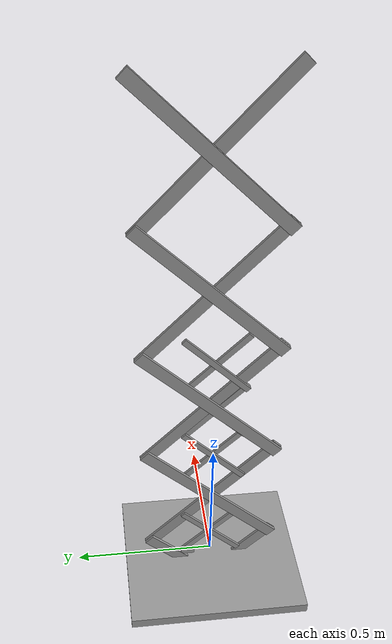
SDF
<?xml version='1.0'?>
<sdf version='1.6'>
  <model name='Robordion_leg_2'>
    <link name='link_0'>
      <pose frame=''>-0.007203 -0.002325 -0.144647 0.77 -0 0</pose>
      <inertial>
        <mass>0.00028808</mass>
        <inertia>
          <ixx>1.032e-05</ixx>
          <ixy>0</ixy>
          <ixz>0</ixz>
          <iyy>4e-08</iyy>
          <iyz>0</iyz>
          <izz>1.028e-05</izz>
        </inertia>
        <pose frame=''>0 0 0 0 -0 0</pose>
      </inertial>
      <self_collide>0</self_collide>
      <kinematic>0</kinematic>
      <enable_wind>0</enable_wind>
      <gravity>1</gravity>
      <visual name='visual'>
        <pose frame=''>0 0 0 0 -0 0</pose>
        <geometry>
          <box>
            <size>0.010804 0.654301 0.040827</size>
          </box>
        </geometry>
        <material>
          <lighting>1</lighting>
          <script>
            <uri>file://media/materials/scripts/gazebo.material</uri>
            <name>Gazebo/Grey</name>
          </script>
          <ambient>0.3 0.3 0.3 1</ambient>
          <diffuse>0.7 0.7 0.7 1</diffuse>
          <specular>0.01 0.01 0.01 1</specular>
          <emissive>0 0 0 1</emissive>
          <shader type='vertex'>
            <normal_map>__default__</normal_map>
          </shader>
        </material>
        <cast_shadows>1</cast_shadows>
        <transparency>0</transparency>
      </visual>
      <collision name='collision'>
        <laser_retro>0</laser_retro>
        <max_contacts>10</max_contacts>
        <pose frame=''>0 0 0 0 -0 0</pose>
        <geometry>
          <box>
            <size>0.010804 0.654301 0.040827</size>
          </box>
        </geometry>
        <surface>
          <friction>
            <ode>
              <mu>1</mu>
              <mu2>1</mu2>
              <fdir1>0 0 0</fdir1>
              <slip1>0</slip1>
              <slip2>0</slip2>
            </ode>
            <torsional>
              <coefficient>1</coefficient>
              <patch_radius>0</patch_radius>
              <surface_radius>0</surface_radius>
              <use_patch_radius>1</use_patch_radius>
              <ode>
                <slip>0</slip>
              </ode>
            </torsional>
          </friction>
          <bounce>
            <restitution_coefficient>0</restitution_coefficient>
            <threshold>1e+06</threshold>
          </bounce>
          <contact>
            <collide_without_contact>0</collide_without_contact>
            <collide_without_contact_bitmask>1</collide_without_contact_bitmask>
            <collide_bitmask>1</collide_bitmask>
            <ode>
              <soft_cfm>0</soft_cfm>
              <soft_erp>0.2</soft_erp>
              <kp>1e+13</kp>
              <kd>1</kd>
              <max_vel>0.01</max_vel>
              <min_depth>0</min_depth>
            </ode>
            <bullet>
              <split_impulse>1</split_impulse>
              <split_impulse_penetration_threshold>-0.01</split_impulse_penetration_threshold>
              <soft_cfm>0</soft_cfm>
              <soft_erp>0.2</soft_erp>
              <kp>1e+13</kp>
              <kd>1</kd>
            </bullet>
          </contact>
        </surface>
      </collision>
    </link>
    <link name='link_0_1'>
      <inertial>
        <mass>7600</mass>
        <inertia>
          <ixx>1266.67</ixx>
          <ixy>0</ixy>
          <ixz>0</ixz>
          <iyy>1266.67</iyy>
          <iyz>0</iyz>
          <izz>1266.67</izz>
        </inertia>
        <pose frame=''>0 0 0 0 -0 0</pose>
      </inertial>
      <pose frame=''>0.005 0 0.098994 -0.785398 0 0</pose>
      <gravity>1</gravity>
      <self_collide>0</self_collide>
      <kinematic>0</kinematic>
      <enable_wind>0</enable_wind>
      <visual name='visual'>
        <pose frame=''>0 0 0 0 -0 0</pose>
        <geometry>
          <box>
            <size>0.01 0.3 0.02</size>
          </box>
        </geometry>
        <material>
          <lighting>1</lighting>
          <script>
            <uri>file://media/materials/scripts/gazebo.material</uri>
            <name>Gazebo/Grey</name>
          </script>
          <ambient>0.3 0.3 0.3 1</ambient>
          <diffuse>0.7 0.7 0.7 1</diffuse>
          <specular>0.01 0.01 0.01 1</specular>
          <emissive>0 0 0 1</emissive>
          <shader type='vertex'>
            <normal_map>__default__</normal_map>
          </shader>
        </material>
        <cast_shadows>1</cast_shadows>
        <transparency>0</transparency>
      </visual>
      <collision name='collision'>
        <laser_retro>0</laser_retro>
        <max_contacts>10</max_contacts>
        <pose frame=''>0 0 0 0 -0 0</pose>
        <geometry>
          <box>
            <size>0.01 0.3 0.02</size>
          </box>
        </geometry>
        <surface>
          <friction>
            <ode>
              <mu>1</mu>
              <mu2>1</mu2>
              <fdir1>0 0 0</fdir1>
              <slip1>0</slip1>
              <slip2>0</slip2>
            </ode>
            <torsional>
              <coefficient>1</coefficient>
              <patch_radius>0</patch_radius>
              <surface_radius>0</surface_radius>
              <use_patch_radius>1</use_patch_radius>
              <ode>
                <slip>0</slip>
              </ode>
            </torsional>
          </friction>
          <bounce>
            <restitution_coefficient>0</restitution_coefficient>
            <threshold>1e+06</threshold>
          </bounce>
          <contact>
            <collide_without_contact>0</collide_without_contact>
            <collide_without_contact_bitmask>1</collide_without_contact_bitmask>
            <collide_bitmask>1</collide_bitmask>
            <ode>
              <soft_cfm>0</soft_cfm>
              <soft_erp>0.2</soft_erp>
              <kp>1e+13</kp>
              <kd>1</kd>
              <max_vel>0.01</max_vel>
              <min_depth>0</min_depth>
            </ode>
            <bullet>
              <split_impulse>1</split_impulse>
              <split_impulse_penetration_threshold>-0.01</split_impulse_penetration_threshold>
              <soft_cfm>0</soft_cfm>
              <soft_erp>0.2</soft_erp>
              <kp>1e+13</kp>
              <kd>1</kd>
            </bullet>
          </contact>
        </surface>
      </collision>
    </link>
    <link name='link_0_1_clone'>
      <inertial>
        <mass>7600</mass>
        <inertia>
          <ixx>1266.67</ixx>
          <ixy>0</ixy>
          <ixz>0</ixz>
          <iyy>1266.67</iyy>
          <iyz>0</iyz>
          <izz>1266.67</izz>
        </inertia>
        <pose frame=''>0 0 0 0 -0 0</pose>
      </inertial>
      <pose frame=''>-0.005 0 0.098994 0.785398 -0 0</pose>
      <gravity>1</gravity>
      <self_collide>0</self_collide>
      <kinematic>0</kinematic>
      <enable_wind>0</enable_wind>
      <visual name='visual_0'>
        <pose frame=''>0 0 0 0 -0 0</pose>
        <geometry>
          <box>
            <size>0.01 0.3 0.02</size>
          </box>
        </geometry>
        <material>
          <lighting>1</lighting>
          <script>
            <uri>file://media/materials/scripts/gazebo.material</uri>
            <name>Gazebo/Grey</name>
          </script>
          <ambient>0.3 0.3 0.3 1</ambient>
          <diffuse>0.7 0.7 0.7 1</diffuse>
          <specular>0.01 0.01 0.01 1</specular>
          <emissive>0 0 0 1</emissive>
          <shader type='vertex'>
            <normal_map>__default__</normal_map>
          </shader>
        </material>
        <cast_shadows>1</cast_shadows>
        <transparency>0</transparency>
      </visual>
      <collision name='collision'>
        <laser_retro>0</laser_retro>
        <max_contacts>10</max_contacts>
        <pose frame=''>0 0 0 0 -0 0</pose>
        <geometry>
          <box>
            <size>0.01 0.3 0.02</size>
          </box>
        </geometry>
        <surface>
          <friction>
            <ode>
              <mu>1</mu>
              <mu2>1</mu2>
              <fdir1>0 0 0</fdir1>
              <slip1>0</slip1>
              <slip2>0</slip2>
            </ode>
            <torsional>
              <coefficient>1</coefficient>
              <patch_radius>0</patch_radius>
              <surface_radius>0</surface_radius>
              <use_patch_radius>1</use_patch_radius>
              <ode>
                <slip>0</slip>
              </ode>
            </torsional>
          </friction>
          <bounce>
            <restitution_coefficient>0</restitution_coefficient>
            <threshold>1e+06</threshold>
          </bounce>
          <contact>
            <collide_without_contact>0</collide_without_contact>
            <collide_without_contact_bitmask>1</collide_without_contact_bitmask>
            <collide_bitmask>1</collide_bitmask>
            <ode>
              <soft_cfm>0</soft_cfm>
              <soft_erp>0.2</soft_erp>
              <kp>1e+13</kp>
              <kd>1</kd>
              <max_vel>0.01</max_vel>
              <min_depth>0</min_depth>
            </ode>
            <bullet>
              <split_impulse>1</split_impulse>
              <split_impulse_penetration_threshold>-0.01</split_impulse_penetration_threshold>
              <soft_cfm>0</soft_cfm>
              <soft_erp>0.2</soft_erp>
              <kp>1e+13</kp>
              <kd>1</kd>
            </bullet>
          </contact>
        </surface>
      </collision>
    </link>
    <link name='link_0_1_clone_0'>
      <inertial>
        <mass>7600</mass>
        <inertia>
          <ixx>1266.67</ixx>
          <ixy>0</ixy>
          <ixz>0</ixz>
          <iyy>1266.67</iyy>
          <iyz>0</iyz>
          <izz>1266.67</izz>
        </inertia>
        <pose frame=''>0 0 0 0 -0 0</pose>
      </inertial>
      <pose frame=''>0.005 0 0.296984 -0.785398 0 0</pose>
      <gravity>1</gravity>
      <self_collide>0</self_collide>
      <kinematic>0</kinematic>
      <enable_wind>0</enable_wind>
      <visual name='visual_0'>
        <pose frame=''>0 0 0 0 -0 0</pose>
        <geometry>
          <box>
            <size>0.01 0.3 0.02</size>
          </box>
        </geometry>
        <material>
          <lighting>1</lighting>
          <script>
            <uri>file://media/materials/scripts/gazebo.material</uri>
            <name>Gazebo/Grey</name>
          </script>
          <ambient>0.3 0.3 0.3 1</ambient>
          <diffuse>0.7 0.7 0.7 1</diffuse>
          <specular>0.01 0.01 0.01 1</specular>
          <emissive>0 0 0 1</emissive>
          <shader type='vertex'>
            <normal_map>__default__</normal_map>
          </shader>
        </material>
        <cast_shadows>1</cast_shadows>
        <transparency>0</transparency>
      </visual>
      <collision name='collision'>
        <laser_retro>0</laser_retro>
        <max_contacts>10</max_contacts>
        <pose frame=''>0 0 0 0 -0 0</pose>
        <geometry>
          <box>
            <size>0.01 0.3 0.02</size>
          </box>
        </geometry>
        <surface>
          <friction>
            <ode>
              <mu>1</mu>
              <mu2>1</mu2>
              <fdir1>0 0 0</fdir1>
              <slip1>0</slip1>
              <slip2>0</slip2>
            </ode>
            <torsional>
              <coefficient>1</coefficient>
              <patch_radius>0</patch_radius>
              <surface_radius>0</surface_radius>
              <use_patch_radius>1</use_patch_radius>
              <ode>
                <slip>0</slip>
              </ode>
            </torsional>
          </friction>
          <bounce>
            <restitution_coefficient>0</restitution_coefficient>
            <threshold>1e+06</threshold>
          </bounce>
          <contact>
            <collide_without_contact>0</collide_without_contact>
            <collide_without_contact_bitmask>1</collide_without_contact_bitmask>
            <collide_bitmask>1</collide_bitmask>
            <ode>
              <soft_cfm>0</soft_cfm>
              <soft_erp>0.2</soft_erp>
              <kp>1e+13</kp>
              <kd>1</kd>
              <max_vel>0.01</max_vel>
              <min_depth>0</min_depth>
            </ode>
            <bullet>
              <split_impulse>1</split_impulse>
              <split_impulse_penetration_threshold>-0.01</split_impulse_penetration_threshold>
              <soft_cfm>0</soft_cfm>
              <soft_erp>0.2</soft_erp>
              <kp>1e+13</kp>
              <kd>1</kd>
            </bullet>
          </contact>
        </surface>
      </collision>
    </link>
    <link name='link_0_1_clone_clone'>
      <inertial>
        <mass>7600</mass>
        <inertia>
          <ixx>1266.67</ixx>
          <ixy>0</ixy>
          <ixz>0</ixz>
          <iyy>1266.67</iyy>
          <iyz>0</iyz>
          <izz>1266.67</izz>
        </inertia>
        <pose frame=''>0 0 0 0 -0 0</pose>
      </inertial>
      <pose frame=''>-0.005 0 0.296984 0.785398 -0 0</pose>
      <gravity>1</gravity>
      <self_collide>0</self_collide>
      <kinematic>0</kinematic>
      <enable_wind>0</enable_wind>
      <visual name='visual_0'>
        <pose frame=''>0 0 0 0 -0 0</pose>
        <geometry>
          <box>
            <size>0.01 0.3 0.02</size>
          </box>
        </geometry>
        <material>
          <lighting>1</lighting>
          <script>
            <uri>file://media/materials/scripts/gazebo.material</uri>
            <name>Gazebo/Grey</name>
          </script>
          <ambient>0.3 0.3 0.3 1</ambient>
          <diffuse>0.7 0.7 0.7 1</diffuse>
          <specular>0.01 0.01 0.01 1</specular>
          <emissive>0 0 0 1</emissive>
          <shader type='vertex'>
            <normal_map>__default__</normal_map>
          </shader>
        </material>
        <cast_shadows>1</cast_shadows>
        <transparency>0</transparency>
      </visual>
      <collision name='collision'>
        <laser_retro>0</laser_retro>
        <max_contacts>10</max_contacts>
        <pose frame=''>0 0 0 0 -0 0</pose>
        <geometry>
          <box>
            <size>0.01 0.3 0.02</size>
          </box>
        </geometry>
        <surface>
          <friction>
            <ode>
              <mu>1</mu>
              <mu2>1</mu2>
              <fdir1>0 0 0</fdir1>
              <slip1>0</slip1>
              <slip2>0</slip2>
            </ode>
            <torsional>
              <coefficient>1</coefficient>
              <patch_radius>0</patch_radius>
              <surface_radius>0</surface_radius>
              <use_patch_radius>1</use_patch_radius>
              <ode>
                <slip>0</slip>
              </ode>
            </torsional>
          </friction>
          <bounce>
            <restitution_coefficient>0</restitution_coefficient>
            <threshold>1e+06</threshold>
          </bounce>
          <contact>
            <collide_without_contact>0</collide_without_contact>
            <collide_without_contact_bitmask>1</collide_without_contact_bitmask>
            <collide_bitmask>1</collide_bitmask>
            <ode>
              <soft_cfm>0</soft_cfm>
              <soft_erp>0.2</soft_erp>
              <kp>1e+13</kp>
              <kd>1</kd>
              <max_vel>0.01</max_vel>
              <min_depth>0</min_depth>
            </ode>
            <bullet>
              <split_impulse>1</split_impulse>
              <split_impulse_penetration_threshold>-0.01</split_impulse_penetration_threshold>
              <soft_cfm>0</soft_cfm>
              <soft_erp>0.2</soft_erp>
              <kp>1e+13</kp>
              <kd>1</kd>
            </bullet>
          </contact>
        </surface>
      </collision>
    </link>
    <link name='link_0_1_clone_clone_0'>
      <inertial>
        <mass>7600</mass>
        <inertia>
          <ixx>1266.67</ixx>
          <ixy>0</ixy>
          <ixz>0</ixz>
          <iyy>1266.67</iyy>
          <iyz>0</iyz>
          <izz>1266.67</izz>
        </inertia>
        <pose frame=''>0 0 0 0 -0 0</pose>
      </inertial>
      <pose frame=''>-0.005 0 0.494974 0.785398 -0 0</pose>
      <gravity>1</gravity>
      <self_collide>0</self_collide>
      <kinematic>0</kinematic>
      <enable_wind>0</enable_wind>
      <visual name='visual_0'>
        <pose frame=''>0 0 0 0 -0 0</pose>
        <geometry>
          <box>
            <size>0.01 0.3 0.02</size>
          </box>
        </geometry>
        <material>
          <lighting>1</lighting>
          <script>
            <uri>file://media/materials/scripts/gazebo.material</uri>
            <name>Gazebo/Grey</name>
          </script>
          <ambient>0.3 0.3 0.3 1</ambient>
          <diffuse>0.7 0.7 0.7 1</diffuse>
          <specular>0.01 0.01 0.01 1</specular>
          <emissive>0 0 0 1</emissive>
          <shader type='vertex'>
            <normal_map>__default__</normal_map>
          </shader>
        </material>
        <cast_shadows>1</cast_shadows>
        <transparency>0</transparency>
      </visual>
      <collision name='collision'>
        <laser_retro>0</laser_retro>
        <max_contacts>10</max_contacts>
        <pose frame=''>0 0 0 0 -0 0</pose>
        <geometry>
          <box>
            <size>0.01 0.3 0.02</size>
          </box>
        </geometry>
        <surface>
          <friction>
            <ode>
              <mu>1</mu>
              <mu2>1</mu2>
              <fdir1>0 0 0</fdir1>
              <slip1>0</slip1>
              <slip2>0</slip2>
            </ode>
            <torsional>
              <coefficient>1</coefficient>
              <patch_radius>0</patch_radius>
              <surface_radius>0</surface_radius>
              <use_patch_radius>1</use_patch_radius>
              <ode>
                <slip>0</slip>
              </ode>
            </torsional>
          </friction>
          <bounce>
            <restitution_coefficient>0</restitution_coefficient>
            <threshold>1e+06</threshold>
          </bounce>
          <contact>
            <collide_without_contact>0</collide_without_contact>
            <collide_without_contact_bitmask>1</collide_without_contact_bitmask>
            <collide_bitmask>1</collide_bitmask>
            <ode>
              <soft_cfm>0</soft_cfm>
              <soft_erp>0.2</soft_erp>
              <kp>1e+13</kp>
              <kd>1</kd>
              <max_vel>0.01</max_vel>
              <min_depth>0</min_depth>
            </ode>
            <bullet>
              <split_impulse>1</split_impulse>
              <split_impulse_penetration_threshold>-0.01</split_impulse_penetration_threshold>
              <soft_cfm>0</soft_cfm>
              <soft_erp>0.2</soft_erp>
              <kp>1e+13</kp>
              <kd>1</kd>
            </bullet>
          </contact>
        </surface>
      </collision>
    </link>
    <link name='link_0_1_clone_clone_0_clone'>
      <inertial>
        <mass>7600</mass>
        <inertia>
          <ixx>1266.67</ixx>
          <ixy>0</ixy>
          <ixz>0</ixz>
          <iyy>1266.67</iyy>
          <iyz>0</iyz>
          <izz>1266.67</izz>
        </inertia>
        <pose frame=''>0 0 0 0 -0 0</pose>
      </inertial>
      <pose frame=''>0.005 0 0.494974 -0.785398 0 0</pose>
      <gravity>1</gravity>
      <self_collide>0</self_collide>
      <kinematic>0</kinematic>
      <enable_wind>0</enable_wind>
      <visual name='visual_0'>
        <pose frame=''>0 0 0 0 -0 0</pose>
        <geometry>
          <box>
            <size>0.01 0.3 0.02</size>
          </box>
        </geometry>
        <material>
          <lighting>1</lighting>
          <script>
            <uri>file://media/materials/scripts/gazebo.material</uri>
            <name>Gazebo/Grey</name>
          </script>
          <ambient>0.3 0.3 0.3 1</ambient>
          <diffuse>0.7 0.7 0.7 1</diffuse>
          <specular>0.01 0.01 0.01 1</specular>
          <emissive>0 0 0 1</emissive>
          <shader type='vertex'>
            <normal_map>__default__</normal_map>
          </shader>
        </material>
        <cast_shadows>1</cast_shadows>
        <transparency>0</transparency>
      </visual>
      <collision name='collision'>
        <laser_retro>0</laser_retro>
        <max_contacts>10</max_contacts>
        <pose frame=''>0 0 0 0 -0 0</pose>
        <geometry>
          <box>
            <size>0.01 0.3 0.02</size>
          </box>
        </geometry>
        <surface>
          <friction>
            <ode>
              <mu>1</mu>
              <mu2>1</mu2>
              <fdir1>0 0 0</fdir1>
              <slip1>0</slip1>
              <slip2>0</slip2>
            </ode>
            <torsional>
              <coefficient>1</coefficient>
              <patch_radius>0</patch_radius>
              <surface_radius>0</surface_radius>
              <use_patch_radius>1</use_patch_radius>
              <ode>
                <slip>0</slip>
              </ode>
            </torsional>
          </friction>
          <bounce>
            <restitution_coefficient>0</restitution_coefficient>
            <threshold>1e+06</threshold>
          </bounce>
          <contact>
            <collide_without_contact>0</collide_without_contact>
            <collide_without_contact_bitmask>1</collide_without_contact_bitmask>
            <collide_bitmask>1</collide_bitmask>
            <ode>
              <soft_cfm>0</soft_cfm>
              <soft_erp>0.2</soft_erp>
              <kp>1e+13</kp>
              <kd>1</kd>
              <max_vel>0.01</max_vel>
              <min_depth>0</min_depth>
            </ode>
            <bullet>
              <split_impulse>1</split_impulse>
              <split_impulse_penetration_threshold>-0.01</split_impulse_penetration_threshold>
              <soft_cfm>0</soft_cfm>
              <soft_erp>0.2</soft_erp>
              <kp>1e+13</kp>
              <kd>1</kd>
            </bullet>
          </contact>
        </surface>
      </collision>
    </link>
    <link name='link_0_1_clone_clone_0_clone_clone'>
      <inertial>
        <mass>7600</mass>
        <inertia>
          <ixx>1266.67</ixx>
          <ixy>0</ixy>
          <ixz>0</ixz>
          <iyy>1266.67</iyy>
          <iyz>0</iyz>
          <izz>1266.67</izz>
        </inertia>
        <pose frame=''>0 0 0 0 -0 0</pose>
      </inertial>
      <pose frame=''>0.005 0 0.692964 -0.785398 0 0</pose>
      <gravity>1</gravity>
      <self_collide>0</self_collide>
      <kinematic>0</kinematic>
      <enable_wind>0</enable_wind>
      <visual name='visual_0'>
        <pose frame=''>0 0 0 0 -0 0</pose>
        <geometry>
          <box>
            <size>0.01 0.3 0.02</size>
          </box>
        </geometry>
        <material>
          <lighting>1</lighting>
          <script>
            <uri>file://media/materials/scripts/gazebo.material</uri>
            <name>Gazebo/Grey</name>
          </script>
          <ambient>0.3 0.3 0.3 1</ambient>
          <diffuse>0.7 0.7 0.7 1</diffuse>
          <specular>0.01 0.01 0.01 1</specular>
          <emissive>0 0 0 1</emissive>
          <shader type='vertex'>
            <normal_map>__default__</normal_map>
          </shader>
        </material>
        <cast_shadows>1</cast_shadows>
        <transparency>0</transparency>
      </visual>
      <collision name='collision'>
        <laser_retro>0</laser_retro>
        <max_contacts>10</max_contacts>
        <pose frame=''>0 0 0 0 -0 0</pose>
        <geometry>
          <box>
            <size>0.01 0.3 0.02</size>
          </box>
        </geometry>
        <surface>
          <friction>
            <ode>
              <mu>1</mu>
              <mu2>1</mu2>
              <fdir1>0 0 0</fdir1>
              <slip1>0</slip1>
              <slip2>0</slip2>
            </ode>
            <torsional>
              <coefficient>1</coefficient>
              <patch_radius>0</patch_radius>
              <surface_radius>0</surface_radius>
              <use_patch_radius>1</use_patch_radius>
              <ode>
                <slip>0</slip>
              </ode>
            </torsional>
          </friction>
          <bounce>
            <restitution_coefficient>0</restitution_coefficient>
            <threshold>1e+06</threshold>
          </bounce>
          <contact>
            <collide_without_contact>0</collide_without_contact>
            <collide_without_contact_bitmask>1</collide_without_contact_bitmask>
            <collide_bitmask>1</collide_bitmask>
            <ode>
              <soft_cfm>0</soft_cfm>
              <soft_erp>0.2</soft_erp>
              <kp>1e+13</kp>
              <kd>1</kd>
              <max_vel>0.01</max_vel>
              <min_depth>0</min_depth>
            </ode>
            <bullet>
              <split_impulse>1</split_impulse>
              <split_impulse_penetration_threshold>-0.01</split_impulse_penetration_threshold>
              <soft_cfm>0</soft_cfm>
              <soft_erp>0.2</soft_erp>
              <kp>1e+13</kp>
              <kd>1</kd>
            </bullet>
          </contact>
        </surface>
      </collision>
    </link>
    <link name='link_0_1_clone_clone_0_clone_clone_clone'>
      <inertial>
        <mass>7600</mass>
        <inertia>
          <ixx>1266.67</ixx>
          <ixy>0</ixy>
          <ixz>0</ixz>
          <iyy>1266.67</iyy>
          <iyz>0</iyz>
          <izz>1266.67</izz>
        </inertia>
        <pose frame=''>0 0 0 0 -0 0</pose>
      </inertial>
      <pose frame=''>-0.005 0 0.692964 0.785398 -0 0</pose>
      <gravity>1</gravity>
      <self_collide>0</self_collide>
      <kinematic>0</kinematic>
      <enable_wind>0</enable_wind>
      <visual name='visual_0'>
        <pose frame=''>0 0 0 0 -0 0</pose>
        <geometry>
          <box>
            <size>0.01 0.3 0.02</size>
          </box>
        </geometry>
        <material>
          <lighting>1</lighting>
          <script>
            <uri>file://media/materials/scripts/gazebo.material</uri>
            <name>Gazebo/Grey</name>
          </script>
          <ambient>0.3 0.3 0.3 1</ambient>
          <diffuse>0.7 0.7 0.7 1</diffuse>
          <specular>0.01 0.01 0.01 1</specular>
          <emissive>0 0 0 1</emissive>
          <shader type='vertex'>
            <normal_map>__default__</normal_map>
          </shader>
        </material>
        <cast_shadows>1</cast_shadows>
        <transparency>0</transparency>
      </visual>
      <collision name='collision'>
        <laser_retro>0</laser_retro>
        <max_contacts>10</max_contacts>
        <pose frame=''>0 0 0 0 -0 0</pose>
        <geometry>
          <box>
            <size>0.01 0.3 0.02</size>
          </box>
        </geometry>
        <surface>
          <friction>
            <ode>
              <mu>1</mu>
              <mu2>1</mu2>
              <fdir1>0 0 0</fdir1>
              <slip1>0</slip1>
              <slip2>0</slip2>
            </ode>
            <torsional>
              <coefficient>1</coefficient>
              <patch_radius>0</patch_radius>
              <surface_radius>0</surface_radius>
              <use_patch_radius>1</use_patch_radius>
              <ode>
                <slip>0</slip>
              </ode>
            </torsional>
          </friction>
          <bounce>
            <restitution_coefficient>0</restitution_coefficient>
            <threshold>1e+06</threshold>
          </bounce>
          <contact>
            <collide_without_contact>0</collide_without_contact>
            <collide_without_contact_bitmask>1</collide_without_contact_bitmask>
            <collide_bitmask>1</collide_bitmask>
            <ode>
              <soft_cfm>0</soft_cfm>
              <soft_erp>0.2</soft_erp>
              <kp>1e+13</kp>
              <kd>1</kd>
              <max_vel>0.01</max_vel>
              <min_depth>0</min_depth>
            </ode>
            <bullet>
              <split_impulse>1</split_impulse>
              <split_impulse_penetration_threshold>-0.01</split_impulse_penetration_threshold>
              <soft_cfm>0</soft_cfm>
              <soft_erp>0.2</soft_erp>
              <kp>1e+13</kp>
              <kd>1</kd>
            </bullet>
          </contact>
        </surface>
      </collision>
    </link>
    <link name='link_0_1_clone_clone_0_clone_clone_clone_0'>
      <inertial>
        <mass>7600</mass>
        <inertia>
          <ixx>1266.67</ixx>
          <ixy>0</ixy>
          <ixz>0</ixz>
          <iyy>1266.67</iyy>
          <iyz>0</iyz>
          <izz>1266.67</izz>
        </inertia>
        <pose frame=''>0 0 0 0 -0 0</pose>
      </inertial>
      <pose frame=''>0.005 0 0.890954 -0.785398 0 0</pose>
      <gravity>1</gravity>
      <self_collide>0</self_collide>
      <kinematic>0</kinematic>
      <enable_wind>0</enable_wind>
      <visual name='visual_0'>
        <pose frame=''>0 0 0 0 -0 0</pose>
        <geometry>
          <box>
            <size>0.01 0.3 0.02</size>
          </box>
        </geometry>
        <material>
          <lighting>1</lighting>
          <script>
            <uri>file://media/materials/scripts/gazebo.material</uri>
            <name>Gazebo/Grey</name>
          </script>
          <ambient>0.3 0.3 0.3 1</ambient>
          <diffuse>0.7 0.7 0.7 1</diffuse>
          <specular>0.01 0.01 0.01 1</specular>
          <emissive>0 0 0 1</emissive>
          <shader type='vertex'>
            <normal_map>__default__</normal_map>
          </shader>
        </material>
        <cast_shadows>1</cast_shadows>
        <transparency>0</transparency>
      </visual>
      <collision name='collision'>
        <laser_retro>0</laser_retro>
        <max_contacts>10</max_contacts>
        <pose frame=''>0 0 0 0 -0 0</pose>
        <geometry>
          <box>
            <size>0.01 0.3 0.02</size>
          </box>
        </geometry>
        <surface>
          <friction>
            <ode>
              <mu>1</mu>
              <mu2>1</mu2>
              <fdir1>0 0 0</fdir1>
              <slip1>0</slip1>
              <slip2>0</slip2>
            </ode>
            <torsional>
              <coefficient>1</coefficient>
              <patch_radius>0</patch_radius>
              <surface_radius>0</surface_radius>
              <use_patch_radius>1</use_patch_radius>
              <ode>
                <slip>0</slip>
              </ode>
            </torsional>
          </friction>
          <bounce>
            <restitution_coefficient>0</restitution_coefficient>
            <threshold>1e+06</threshold>
          </bounce>
          <contact>
            <collide_without_contact>0</collide_without_contact>
            <collide_without_contact_bitmask>1</collide_without_contact_bitmask>
            <collide_bitmask>1</collide_bitmask>
            <ode>
              <soft_cfm>0</soft_cfm>
              <soft_erp>0.2</soft_erp>
              <kp>1e+13</kp>
              <kd>1</kd>
              <max_vel>0.01</max_vel>
              <min_depth>0</min_depth>
            </ode>
            <bullet>
              <split_impulse>1</split_impulse>
              <split_impulse_penetration_threshold>-0.01</split_impulse_penetration_threshold>
              <soft_cfm>0</soft_cfm>
              <soft_erp>0.2</soft_erp>
              <kp>1e+13</kp>
              <kd>1</kd>
            </bullet>
          </contact>
        </surface>
      </collision>
    </link>
    <link name='link_0_1_clone_clone_0_clone_clone_clone_0_clone'>
      <inertial>
        <mass>7600</mass>
        <inertia>
          <ixx>1266.67</ixx>
          <ixy>0</ixy>
          <ixz>0</ixz>
          <iyy>1266.67</iyy>
          <iyz>0</iyz>
          <izz>1266.67</izz>
        </inertia>
        <pose frame=''>0 0 0 0 -0 0</pose>
      </inertial>
      <pose frame=''>-0.005 0 0.890954 0.785398 -0 0</pose>
      <gravity>1</gravity>
      <self_collide>0</self_collide>
      <kinematic>0</kinematic>
      <enable_wind>0</enable_wind>
      <visual name='visual_0'>
        <pose frame=''>0 0 0 0 -0 0</pose>
        <geometry>
          <box>
            <size>0.01 0.3 0.02</size>
          </box>
        </geometry>
        <material>
          <lighting>1</lighting>
          <script>
            <uri>file://media/materials/scripts/gazebo.material</uri>
            <name>Gazebo/Grey</name>
          </script>
          <ambient>0.3 0.3 0.3 1</ambient>
          <diffuse>0.7 0.7 0.7 1</diffuse>
          <specular>0.01 0.01 0.01 1</specular>
          <emissive>0 0 0 1</emissive>
          <shader type='vertex'>
            <normal_map>__default__</normal_map>
          </shader>
        </material>
        <cast_shadows>1</cast_shadows>
        <transparency>0</transparency>
      </visual>
      <collision name='collision'>
        <laser_retro>0</laser_retro>
        <max_contacts>10</max_contacts>
        <pose frame=''>0 0 0 0 -0 0</pose>
        <geometry>
          <box>
            <size>0.01 0.3 0.02</size>
          </box>
        </geometry>
        <surface>
          <friction>
            <ode>
              <mu>1</mu>
              <mu2>1</mu2>
              <fdir1>0 0 0</fdir1>
              <slip1>0</slip1>
              <slip2>0</slip2>
            </ode>
            <torsional>
              <coefficient>1</coefficient>
              <patch_radius>0</patch_radius>
              <surface_radius>0</surface_radius>
              <use_patch_radius>1</use_patch_radius>
              <ode>
                <slip>0</slip>
              </ode>
            </torsional>
          </friction>
          <bounce>
            <restitution_coefficient>0</restitution_coefficient>
            <threshold>1e+06</threshold>
          </bounce>
          <contact>
            <collide_without_contact>0</collide_without_contact>
            <collide_without_contact_bitmask>1</collide_without_contact_bitmask>
            <collide_bitmask>1</collide_bitmask>
            <ode>
              <soft_cfm>0</soft_cfm>
              <soft_erp>0.2</soft_erp>
              <kp>1e+13</kp>
              <kd>1</kd>
              <max_vel>0.01</max_vel>
              <min_depth>0</min_depth>
            </ode>
            <bullet>
              <split_impulse>1</split_impulse>
              <split_impulse_penetration_threshold>-0.01</split_impulse_penetration_threshold>
              <soft_cfm>0</soft_cfm>
              <soft_erp>0.2</soft_erp>
              <kp>1e+13</kp>
              <kd>1</kd>
            </bullet>
          </contact>
        </surface>
      </collision>
    </link>
    <link name='link_0_clone'>
      <pose frame=''>0.003601 -0.002325 -0.144647 -0.800796 0 0</pose>
      <inertial>
        <mass>0.00028808</mass>
        <inertia>
          <ixx>1.032e-05</ixx>
          <ixy>0</ixy>
          <ixz>0</ixz>
          <iyy>4e-08</iyy>
          <iyz>0</iyz>
          <izz>1.028e-05</izz>
        </inertia>
        <pose frame=''>0 0 0 0 -0 0</pose>
      </inertial>
      <self_collide>0</self_collide>
      <kinematic>0</kinematic>
      <enable_wind>0</enable_wind>
      <gravity>1</gravity>
      <visual name='visual'>
        <pose frame=''>0 0 0 0 -0 0</pose>
        <geometry>
          <box>
            <size>0.010804 0.654301 0.040827</size>
          </box>
        </geometry>
        <material>
          <lighting>1</lighting>
          <script>
            <uri>file://media/materials/scripts/gazebo.material</uri>
            <name>Gazebo/Grey</name>
          </script>
          <ambient>0.3 0.3 0.3 1</ambient>
          <diffuse>0.7 0.7 0.7 1</diffuse>
          <specular>0.01 0.01 0.01 1</specular>
          <emissive>0 0 0 1</emissive>
          <shader type='vertex'>
            <normal_map>__default__</normal_map>
          </shader>
        </material>
        <cast_shadows>1</cast_shadows>
        <transparency>0</transparency>
      </visual>
      <collision name='collision'>
        <laser_retro>0</laser_retro>
        <max_contacts>10</max_contacts>
        <pose frame=''>0 0 0 0 -0 0</pose>
        <geometry>
          <box>
            <size>0.010804 0.654301 0.040827</size>
          </box>
        </geometry>
        <surface>
          <friction>
            <ode>
              <mu>1</mu>
              <mu2>1</mu2>
              <fdir1>0 0 0</fdir1>
              <slip1>0</slip1>
              <slip2>0</slip2>
            </ode>
            <torsional>
              <coefficient>1</coefficient>
              <patch_radius>0</patch_radius>
              <surface_radius>0</surface_radius>
              <use_patch_radius>1</use_patch_radius>
              <ode>
                <slip>0</slip>
              </ode>
            </torsional>
          </friction>
          <bounce>
            <restitution_coefficient>0</restitution_coefficient>
            <threshold>1e+06</threshold>
          </bounce>
          <contact>
            <collide_without_contact>0</collide_without_contact>
            <collide_without_contact_bitmask>1</collide_without_contact_bitmask>
            <collide_bitmask>1</collide_bitmask>
            <ode>
              <soft_cfm>0</soft_cfm>
              <soft_erp>0.2</soft_erp>
              <kp>1e+13</kp>
              <kd>1</kd>
              <max_vel>0.01</max_vel>
              <min_depth>0</min_depth>
            </ode>
            <bullet>
              <split_impulse>1</split_impulse>
              <split_impulse_penetration_threshold>-0.01</split_impulse_penetration_threshold>
              <soft_cfm>0</soft_cfm>
              <soft_erp>0.2</soft_erp>
              <kp>1e+13</kp>
              <kd>1</kd>
            </bullet>
          </contact>
        </surface>
      </collision>
    </link>
    <link name='link_0_clone_0'>
      <pose frame=''>-0.007203 0.005127 0.29548 0.77 -0 0</pose>
      <inertial>
        <mass>0.00028808</mass>
        <inertia>
          <ixx>1.032e-05</ixx>
          <ixy>0</ixy>
          <ixz>0</ixz>
          <iyy>4e-08</iyy>
          <iyz>0</iyz>
          <izz>1.028e-05</izz>
        </inertia>
        <pose frame=''>0 0 0 0 -0 0</pose>
      </inertial>
      <self_collide>0</self_collide>
      <kinematic>0</kinematic>
      <enable_wind>0</enable_wind>
      <gravity>1</gravity>
      <visual name='visual'>
        <pose frame=''>0 0 0 0 -0 0</pose>
        <geometry>
          <box>
            <size>0.010804 0.654301 0.040827</size>
          </box>
        </geometry>
        <material>
          <lighting>1</lighting>
          <script>
            <uri>file://media/materials/scripts/gazebo.material</uri>
            <name>Gazebo/Grey</name>
          </script>
          <ambient>0.3 0.3 0.3 1</ambient>
          <diffuse>0.7 0.7 0.7 1</diffuse>
          <specular>0.01 0.01 0.01 1</specular>
          <emissive>0 0 0 1</emissive>
          <shader type='vertex'>
            <normal_map>__default__</normal_map>
          </shader>
        </material>
        <cast_shadows>1</cast_shadows>
        <transparency>0</transparency>
      </visual>
      <collision name='collision'>
        <laser_retro>0</laser_retro>
        <max_contacts>10</max_contacts>
        <pose frame=''>0 0 0 0 -0 0</pose>
        <geometry>
          <box>
            <size>0.010804 0.654301 0.040827</size>
          </box>
        </geometry>
        <surface>
          <friction>
            <ode>
              <mu>1</mu>
              <mu2>1</mu2>
              <fdir1>0 0 0</fdir1>
              <slip1>0</slip1>
              <slip2>0</slip2>
            </ode>
            <torsional>
              <coefficient>1</coefficient>
              <patch_radius>0</patch_radius>
              <surface_radius>0</surface_radius>
              <use_patch_radius>1</use_patch_radius>
              <ode>
                <slip>0</slip>
              </ode>
            </torsional>
          </friction>
          <bounce>
            <restitution_coefficient>0</restitution_coefficient>
            <threshold>1e+06</threshold>
          </bounce>
          <contact>
            <collide_without_contact>0</collide_without_contact>
            <collide_without_contact_bitmask>1</collide_without_contact_bitmask>
            <collide_bitmask>1</collide_bitmask>
            <ode>
              <soft_cfm>0</soft_cfm>
              <soft_erp>0.2</soft_erp>
              <kp>1e+13</kp>
              <kd>1</kd>
              <max_vel>0.01</max_vel>
              <min_depth>0</min_depth>
            </ode>
            <bullet>
              <split_impulse>1</split_impulse>
              <split_impulse_penetration_threshold>-0.01</split_impulse_penetration_threshold>
              <soft_cfm>0</soft_cfm>
              <soft_erp>0.2</soft_erp>
              <kp>1e+13</kp>
              <kd>1</kd>
            </bullet>
          </contact>
        </surface>
      </collision>
    </link>
    <link name='link_0_clone_0_clone'>
      <pose frame=''>-0.007203 0.012117 0.720098 0.77 -0 0</pose>
      <inertial>
        <mass>0.00028808</mass>
        <inertia>
          <ixx>1.032e-05</ixx>
          <ixy>0</ixy>
          <ixz>0</ixz>
          <iyy>4e-08</iyy>
          <iyz>0</iyz>
          <izz>1.028e-05</izz>
        </inertia>
        <pose frame=''>0 0 0 0 -0 0</pose>
      </inertial>
      <self_collide>0</self_collide>
      <kinematic>0</kinematic>
      <enable_wind>0</enable_wind>
      <gravity>1</gravity>
      <visual name='visual'>
        <pose frame=''>0 0 0 0 -0 0</pose>
        <geometry>
          <box>
            <size>0.010804 0.654301 0.040827</size>
          </box>
        </geometry>
        <material>
          <lighting>1</lighting>
          <script>
            <uri>file://media/materials/scripts/gazebo.material</uri>
            <name>Gazebo/Grey</name>
          </script>
          <ambient>0.3 0.3 0.3 1</ambient>
          <diffuse>0.7 0.7 0.7 1</diffuse>
          <specular>0.01 0.01 0.01 1</specular>
          <emissive>0 0 0 1</emissive>
          <shader type='vertex'>
            <normal_map>__default__</normal_map>
          </shader>
        </material>
        <cast_shadows>1</cast_shadows>
        <transparency>0</transparency>
      </visual>
      <collision name='collision'>
        <laser_retro>0</laser_retro>
        <max_contacts>10</max_contacts>
        <pose frame=''>0 0 0 0 -0 0</pose>
        <geometry>
          <box>
            <size>0.010804 0.654301 0.040827</size>
          </box>
        </geometry>
        <surface>
          <friction>
            <ode>
              <mu>1</mu>
              <mu2>1</mu2>
              <fdir1>0 0 0</fdir1>
              <slip1>0</slip1>
              <slip2>0</slip2>
            </ode>
            <torsional>
              <coefficient>1</coefficient>
              <patch_radius>0</patch_radius>
              <surface_radius>0</surface_radius>
              <use_patch_radius>1</use_patch_radius>
              <ode>
                <slip>0</slip>
              </ode>
            </torsional>
          </friction>
          <bounce>
            <restitution_coefficient>0</restitution_coefficient>
            <threshold>1e+06</threshold>
          </bounce>
          <contact>
            <collide_without_contact>0</collide_without_contact>
            <collide_without_contact_bitmask>1</collide_without_contact_bitmask>
            <collide_bitmask>1</collide_bitmask>
            <ode>
              <soft_cfm>0</soft_cfm>
              <soft_erp>0.2</soft_erp>
              <kp>1e+13</kp>
              <kd>1</kd>
              <max_vel>0.01</max_vel>
              <min_depth>0</min_depth>
            </ode>
            <bullet>
              <split_impulse>1</split_impulse>
              <split_impulse_penetration_threshold>-0.01</split_impulse_penetration_threshold>
              <soft_cfm>0</soft_cfm>
              <soft_erp>0.2</soft_erp>
              <kp>1e+13</kp>
              <kd>1</kd>
            </bullet>
          </contact>
        </surface>
      </collision>
    </link>
    <link name='link_0_clone_0_clone_clone'>
      <pose frame=''>-0.007234 0.01887 1.1597 0.77 -0 0</pose>
      <inertial>
        <mass>0.00028808</mass>
        <inertia>
          <ixx>1.032e-05</ixx>
          <ixy>0</ixy>
          <ixz>0</ixz>
          <iyy>4e-08</iyy>
          <iyz>0</iyz>
          <izz>1.028e-05</izz>
        </inertia>
        <pose frame=''>0 0 0 0 -0 0</pose>
      </inertial>
      <self_collide>0</self_collide>
      <kinematic>0</kinematic>
      <enable_wind>0</enable_wind>
      <gravity>1</gravity>
      <visual name='visual'>
        <pose frame=''>0 0 0 0 -0 0</pose>
        <geometry>
          <box>
            <size>0.010804 0.654301 0.040827</size>
          </box>
        </geometry>
        <material>
          <lighting>1</lighting>
          <script>
            <uri>file://media/materials/scripts/gazebo.material</uri>
            <name>Gazebo/Grey</name>
          </script>
          <ambient>0.3 0.3 0.3 1</ambient>
          <diffuse>0.7 0.7 0.7 1</diffuse>
          <specular>0.01 0.01 0.01 1</specular>
          <emissive>0 0 0 1</emissive>
          <shader type='vertex'>
            <normal_map>__default__</normal_map>
          </shader>
        </material>
        <cast_shadows>1</cast_shadows>
        <transparency>0</transparency>
      </visual>
      <collision name='collision'>
        <laser_retro>0</laser_retro>
        <max_contacts>10</max_contacts>
        <pose frame=''>0 0 0 0 -0 0</pose>
        <geometry>
          <box>
            <size>0.010804 0.654301 0.040827</size>
          </box>
        </geometry>
        <surface>
          <friction>
            <ode>
              <mu>1</mu>
              <mu2>1</mu2>
              <fdir1>0 0 0</fdir1>
              <slip1>0</slip1>
              <slip2>0</slip2>
            </ode>
            <torsional>
              <coefficient>1</coefficient>
              <patch_radius>0</patch_radius>
              <surface_radius>0</surface_radius>
              <use_patch_radius>1</use_patch_radius>
              <ode>
                <slip>0</slip>
              </ode>
            </torsional>
          </friction>
          <bounce>
            <restitution_coefficient>0</restitution_coefficient>
            <threshold>1e+06</threshold>
          </bounce>
          <contact>
            <collide_without_contact>0</collide_without_contact>
            <collide_without_contact_bitmask>1</collide_without_contact_bitmask>
            <collide_bitmask>1</collide_bitmask>
            <ode>
              <soft_cfm>0</soft_cfm>
              <soft_erp>0.2</soft_erp>
              <kp>1e+13</kp>
              <kd>1</kd>
              <max_vel>0.01</max_vel>
              <min_depth>0</min_depth>
            </ode>
            <bullet>
              <split_impulse>1</split_impulse>
              <split_impulse_penetration_threshold>-0.01</split_impulse_penetration_threshold>
              <soft_cfm>0</soft_cfm>
              <soft_erp>0.2</soft_erp>
              <kp>1e+13</kp>
              <kd>1</kd>
            </bullet>
          </contact>
        </surface>
      </collision>
    </link>
    <link name='link_0_clone_0_clone_clone_clone'>
      <pose frame=''>-0.007234 0.025984 1.58764 0.77 -0 0</pose>
      <inertial>
        <mass>0.00028808</mass>
        <inertia>
          <ixx>1.032e-05</ixx>
          <ixy>0</ixy>
          <ixz>0</ixz>
          <iyy>4e-08</iyy>
          <iyz>0</iyz>
          <izz>1.028e-05</izz>
        </inertia>
        <pose frame=''>0 0 0 0 -0 0</pose>
      </inertial>
      <self_collide>0</self_collide>
      <kinematic>0</kinematic>
      <enable_wind>0</enable_wind>
      <gravity>1</gravity>
      <visual name='visual'>
        <pose frame=''>0 0 0 0 -0 0</pose>
        <geometry>
          <box>
            <size>0.010804 0.654301 0.040827</size>
          </box>
        </geometry>
        <material>
          <lighting>1</lighting>
          <script>
            <uri>file://media/materials/scripts/gazebo.material</uri>
            <name>Gazebo/Grey</name>
          </script>
          <ambient>0.3 0.3 0.3 1</ambient>
          <diffuse>0.7 0.7 0.7 1</diffuse>
          <specular>0.01 0.01 0.01 1</specular>
          <emissive>0 0 0 1</emissive>
          <shader type='vertex'>
            <normal_map>__default__</normal_map>
          </shader>
        </material>
        <cast_shadows>1</cast_shadows>
        <transparency>0</transparency>
      </visual>
      <collision name='collision'>
        <laser_retro>0</laser_retro>
        <max_contacts>10</max_contacts>
        <pose frame=''>0 0 0 0 -0 0</pose>
        <geometry>
          <box>
            <size>0.010804 0.654301 0.040827</size>
          </box>
        </geometry>
        <surface>
          <friction>
            <ode>
              <mu>1</mu>
              <mu2>1</mu2>
              <fdir1>0 0 0</fdir1>
              <slip1>0</slip1>
              <slip2>0</slip2>
            </ode>
            <torsional>
              <coefficient>1</coefficient>
              <patch_radius>0</patch_radius>
              <surface_radius>0</surface_radius>
              <use_patch_radius>1</use_patch_radius>
              <ode>
                <slip>0</slip>
              </ode>
            </torsional>
          </friction>
          <bounce>
            <restitution_coefficient>0</restitution_coefficient>
            <threshold>1e+06</threshold>
          </bounce>
          <contact>
            <collide_without_contact>0</collide_without_contact>
            <collide_without_contact_bitmask>1</collide_without_contact_bitmask>
            <collide_bitmask>1</collide_bitmask>
            <ode>
              <soft_cfm>0</soft_cfm>
              <soft_erp>0.2</soft_erp>
              <kp>1e+13</kp>
              <kd>1</kd>
              <max_vel>0.01</max_vel>
              <min_depth>0</min_depth>
            </ode>
            <bullet>
              <split_impulse>1</split_impulse>
              <split_impulse_penetration_threshold>-0.01</split_impulse_penetration_threshold>
              <soft_cfm>0</soft_cfm>
              <soft_erp>0.2</soft_erp>
              <kp>1e+13</kp>
              <kd>1</kd>
            </bullet>
          </contact>
        </surface>
      </collision>
    </link>
    <link name='link_0_clone_clone'>
      <pose frame=''>0.003601 0.005127 0.288801 -0.800796 0 0</pose>
      <inertial>
        <mass>0.00028808</mass>
        <inertia>
          <ixx>1.032e-05</ixx>
          <ixy>0</ixy>
          <ixz>0</ixz>
          <iyy>4e-08</iyy>
          <iyz>0</iyz>
          <izz>1.028e-05</izz>
        </inertia>
        <pose frame=''>0 0 0 0 -0 0</pose>
      </inertial>
      <self_collide>0</self_collide>
      <kinematic>0</kinematic>
      <enable_wind>0</enable_wind>
      <gravity>1</gravity>
      <visual name='visual'>
        <pose frame=''>0 0 0 0 -0 0</pose>
        <geometry>
          <box>
            <size>0.010804 0.654301 0.040827</size>
          </box>
        </geometry>
        <material>
          <lighting>1</lighting>
          <script>
            <uri>file://media/materials/scripts/gazebo.material</uri>
            <name>Gazebo/Grey</name>
          </script>
          <ambient>0.3 0.3 0.3 1</ambient>
          <diffuse>0.7 0.7 0.7 1</diffuse>
          <specular>0.01 0.01 0.01 1</specular>
          <emissive>0 0 0 1</emissive>
          <shader type='vertex'>
            <normal_map>__default__</normal_map>
          </shader>
        </material>
        <cast_shadows>1</cast_shadows>
        <transparency>0</transparency>
      </visual>
      <collision name='collision'>
        <laser_retro>0</laser_retro>
        <max_contacts>10</max_contacts>
        <pose frame=''>0 0 0 0 -0 0</pose>
        <geometry>
          <box>
            <size>0.010804 0.654301 0.040827</size>
          </box>
        </geometry>
        <surface>
          <friction>
            <ode>
              <mu>1</mu>
              <mu2>1</mu2>
              <fdir1>0 0 0</fdir1>
              <slip1>0</slip1>
              <slip2>0</slip2>
            </ode>
            <torsional>
              <coefficient>1</coefficient>
              <patch_radius>0</patch_radius>
              <surface_radius>0</surface_radius>
              <use_patch_radius>1</use_patch_radius>
              <ode>
                <slip>0</slip>
              </ode>
            </torsional>
          </friction>
          <bounce>
            <restitution_coefficient>0</restitution_coefficient>
            <threshold>1e+06</threshold>
          </bounce>
          <contact>
            <collide_without_contact>0</collide_without_contact>
            <collide_without_contact_bitmask>1</collide_without_contact_bitmask>
            <collide_bitmask>1</collide_bitmask>
            <ode>
              <soft_cfm>0</soft_cfm>
              <soft_erp>0.2</soft_erp>
              <kp>1e+13</kp>
              <kd>1</kd>
              <max_vel>0.01</max_vel>
              <min_depth>0</min_depth>
            </ode>
            <bullet>
              <split_impulse>1</split_impulse>
              <split_impulse_penetration_threshold>-0.01</split_impulse_penetration_threshold>
              <soft_cfm>0</soft_cfm>
              <soft_erp>0.2</soft_erp>
              <kp>1e+13</kp>
              <kd>1</kd>
            </bullet>
          </contact>
        </surface>
      </collision>
    </link>
    <link name='link_0_clone_clone_0'>
      <pose frame=''>0.003601 0.012116 0.726777 -0.800796 0 0</pose>
      <inertial>
        <mass>0.00028808</mass>
        <inertia>
          <ixx>1.032e-05</ixx>
          <ixy>0</ixy>
          <ixz>0</ixz>
          <iyy>4e-08</iyy>
          <iyz>0</iyz>
          <izz>1.028e-05</izz>
        </inertia>
        <pose frame=''>0 0 0 0 -0 0</pose>
      </inertial>
      <self_collide>0</self_collide>
      <kinematic>0</kinematic>
      <enable_wind>0</enable_wind>
      <gravity>1</gravity>
      <visual name='visual'>
        <pose frame=''>0 0 0 0 -0 0</pose>
        <geometry>
          <box>
            <size>0.010804 0.654301 0.040827</size>
          </box>
        </geometry>
        <material>
          <lighting>1</lighting>
          <script>
            <uri>file://media/materials/scripts/gazebo.material</uri>
            <name>Gazebo/Grey</name>
          </script>
          <ambient>0.3 0.3 0.3 1</ambient>
          <diffuse>0.7 0.7 0.7 1</diffuse>
          <specular>0.01 0.01 0.01 1</specular>
          <emissive>0 0 0 1</emissive>
          <shader type='vertex'>
            <normal_map>__default__</normal_map>
          </shader>
        </material>
        <cast_shadows>1</cast_shadows>
        <transparency>0</transparency>
      </visual>
      <collision name='collision'>
        <laser_retro>0</laser_retro>
        <max_contacts>10</max_contacts>
        <pose frame=''>0 0 0 0 -0 0</pose>
        <geometry>
          <box>
            <size>0.010804 0.654301 0.040827</size>
          </box>
        </geometry>
        <surface>
          <friction>
            <ode>
              <mu>1</mu>
              <mu2>1</mu2>
              <fdir1>0 0 0</fdir1>
              <slip1>0</slip1>
              <slip2>0</slip2>
            </ode>
            <torsional>
              <coefficient>1</coefficient>
              <patch_radius>0</patch_radius>
              <surface_radius>0</surface_radius>
              <use_patch_radius>1</use_patch_radius>
              <ode>
                <slip>0</slip>
              </ode>
            </torsional>
          </friction>
          <bounce>
            <restitution_coefficient>0</restitution_coefficient>
            <threshold>1e+06</threshold>
          </bounce>
          <contact>
            <collide_without_contact>0</collide_without_contact>
            <collide_without_contact_bitmask>1</collide_without_contact_bitmask>
            <collide_bitmask>1</collide_bitmask>
            <ode>
              <soft_cfm>0</soft_cfm>
              <soft_erp>0.2</soft_erp>
              <kp>1e+13</kp>
              <kd>1</kd>
              <max_vel>0.01</max_vel>
              <min_depth>0</min_depth>
            </ode>
            <bullet>
              <split_impulse>1</split_impulse>
              <split_impulse_penetration_threshold>-0.01</split_impulse_penetration_threshold>
              <soft_cfm>0</soft_cfm>
              <soft_erp>0.2</soft_erp>
              <kp>1e+13</kp>
              <kd>1</kd>
            </bullet>
          </contact>
        </surface>
      </collision>
    </link>
    <link name='link_0_clone_clone_0_clone'>
      <pose frame=''>0.00357 0.01887 1.15302 -0.800796 0 0</pose>
      <inertial>
        <mass>0.00028808</mass>
        <inertia>
          <ixx>1.032e-05</ixx>
          <ixy>0</ixy>
          <ixz>0</ixz>
          <iyy>4e-08</iyy>
          <iyz>0</iyz>
          <izz>1.028e-05</izz>
        </inertia>
        <pose frame=''>0 0 0 0 -0 0</pose>
      </inertial>
      <self_collide>0</self_collide>
      <kinematic>0</kinematic>
      <enable_wind>0</enable_wind>
      <gravity>1</gravity>
      <visual name='visual'>
        <pose frame=''>0 0 0 0 -0 0</pose>
        <geometry>
          <box>
            <size>0.010804 0.654301 0.040827</size>
          </box>
        </geometry>
        <material>
          <lighting>1</lighting>
          <script>
            <uri>file://media/materials/scripts/gazebo.material</uri>
            <name>Gazebo/Grey</name>
          </script>
          <ambient>0.3 0.3 0.3 1</ambient>
          <diffuse>0.7 0.7 0.7 1</diffuse>
          <specular>0.01 0.01 0.01 1</specular>
          <emissive>0 0 0 1</emissive>
          <shader type='vertex'>
            <normal_map>__default__</normal_map>
          </shader>
        </material>
        <cast_shadows>1</cast_shadows>
        <transparency>0</transparency>
      </visual>
      <collision name='collision'>
        <laser_retro>0</laser_retro>
        <max_contacts>10</max_contacts>
        <pose frame=''>0 0 0 0 -0 0</pose>
        <geometry>
          <box>
            <size>0.010804 0.654301 0.040827</size>
          </box>
        </geometry>
        <surface>
          <friction>
            <ode>
              <mu>1</mu>
              <mu2>1</mu2>
              <fdir1>0 0 0</fdir1>
              <slip1>0</slip1>
              <slip2>0</slip2>
            </ode>
            <torsional>
              <coefficient>1</coefficient>
              <patch_radius>0</patch_radius>
              <surface_radius>0</surface_radius>
              <use_patch_radius>1</use_patch_radius>
              <ode>
                <slip>0</slip>
              </ode>
            </torsional>
          </friction>
          <bounce>
            <restitution_coefficient>0</restitution_coefficient>
            <threshold>1e+06</threshold>
          </bounce>
          <contact>
            <collide_without_contact>0</collide_without_contact>
            <collide_without_contact_bitmask>1</collide_without_contact_bitmask>
            <collide_bitmask>1</collide_bitmask>
            <ode>
              <soft_cfm>0</soft_cfm>
              <soft_erp>0.2</soft_erp>
              <kp>1e+13</kp>
              <kd>1</kd>
              <max_vel>0.01</max_vel>
              <min_depth>0</min_depth>
            </ode>
            <bullet>
              <split_impulse>1</split_impulse>
              <split_impulse_penetration_threshold>-0.01</split_impulse_penetration_threshold>
              <soft_cfm>0</soft_cfm>
              <soft_erp>0.2</soft_erp>
              <kp>1e+13</kp>
              <kd>1</kd>
            </bullet>
          </contact>
        </surface>
      </collision>
    </link>
    <link name='link_0_clone_clone_0_clone_clone'>
      <pose frame=''>0.00357 0.025752 1.59415 -0.800796 0 0</pose>
      <inertial>
        <mass>0.00028808</mass>
        <inertia>
          <ixx>1.032e-05</ixx>
          <ixy>0</ixy>
          <ixz>0</ixz>
          <iyy>4e-08</iyy>
          <iyz>0</iyz>
          <izz>1.028e-05</izz>
        </inertia>
        <pose frame=''>0 0 0 0 -0 0</pose>
      </inertial>
      <self_collide>0</self_collide>
      <kinematic>0</kinematic>
      <enable_wind>0</enable_wind>
      <gravity>1</gravity>
      <visual name='visual'>
        <pose frame=''>0 0 0 0 -0 0</pose>
        <geometry>
          <box>
            <size>0.010804 0.654301 0.040827</size>
          </box>
        </geometry>
        <material>
          <lighting>1</lighting>
          <script>
            <uri>file://media/materials/scripts/gazebo.material</uri>
            <name>Gazebo/Grey</name>
          </script>
          <ambient>0.3 0.3 0.3 1</ambient>
          <diffuse>0.7 0.7 0.7 1</diffuse>
          <specular>0.01 0.01 0.01 1</specular>
          <emissive>0 0 0 1</emissive>
          <shader type='vertex'>
            <normal_map>__default__</normal_map>
          </shader>
        </material>
        <cast_shadows>1</cast_shadows>
        <transparency>0</transparency>
      </visual>
      <collision name='collision'>
        <laser_retro>0</laser_retro>
        <max_contacts>10</max_contacts>
        <pose frame=''>0 0 0 0 -0 0</pose>
        <geometry>
          <box>
            <size>0.010804 0.654301 0.040827</size>
          </box>
        </geometry>
        <surface>
          <friction>
            <ode>
              <mu>1</mu>
              <mu2>1</mu2>
              <fdir1>0 0 0</fdir1>
              <slip1>0</slip1>
              <slip2>0</slip2>
            </ode>
            <torsional>
              <coefficient>1</coefficient>
              <patch_radius>0</patch_radius>
              <surface_radius>0</surface_radius>
              <use_patch_radius>1</use_patch_radius>
              <ode>
                <slip>0</slip>
              </ode>
            </torsional>
          </friction>
          <bounce>
            <restitution_coefficient>0</restitution_coefficient>
            <threshold>1e+06</threshold>
          </bounce>
          <contact>
            <collide_without_contact>0</collide_without_contact>
            <collide_without_contact_bitmask>1</collide_without_contact_bitmask>
            <collide_bitmask>1</collide_bitmask>
            <ode>
              <soft_cfm>0</soft_cfm>
              <soft_erp>0.2</soft_erp>
              <kp>1e+13</kp>
              <kd>1</kd>
              <max_vel>0.01</max_vel>
              <min_depth>0</min_depth>
            </ode>
            <bullet>
              <split_impulse>1</split_impulse>
              <split_impulse_penetration_threshold>-0.01</split_impulse_penetration_threshold>
              <soft_cfm>0</soft_cfm>
              <soft_erp>0.2</soft_erp>
              <kp>1e+13</kp>
              <kd>1</kd>
            </bullet>
          </contact>
        </surface>
      </collision>
    </link>
    <link name='link_0_clone_clone_1_clone'>
      <pose frame=''>0.014405 0.214205 -0.366629 0 -0 0</pose>
      <inertial>
        <mass>2.27771e-05</mass>
        <inertia>
          <ixx>8.24361e-09</ixx>
          <ixy>0</ixy>
          <ixz>0</ixz>
          <iyy>3.16261e-09</iyy>
          <iyz>0</iyz>
          <izz>5.081e-09</izz>
        </inertia>
        <pose frame=''>0 0 0 0 -0 0</pose>
      </inertial>
      <self_collide>0</self_collide>
      <kinematic>0</kinematic>
      <enable_wind>0</enable_wind>
      <gravity>1</gravity>
      <visual name='visual'>
        <pose frame=''>0 0 0 0 -0 0</pose>
        <geometry>
          <box>
            <size>0.010804 0.051733 0.040827</size>
          </box>
        </geometry>
        <material>
          <lighting>1</lighting>
          <script>
            <uri>file://media/materials/scripts/gazebo.material</uri>
            <name>Gazebo/Grey</name>
          </script>
          <ambient>0.3 0.3 0.3 1</ambient>
          <diffuse>0.7 0.7 0.7 1</diffuse>
          <specular>0.01 0.01 0.01 1</specular>
          <emissive>0 0 0 1</emissive>
          <shader type='vertex'>
            <normal_map>__default__</normal_map>
          </shader>
        </material>
        <cast_shadows>1</cast_shadows>
        <transparency>0</transparency>
      </visual>
      <collision name='collision'>
        <laser_retro>0</laser_retro>
        <max_contacts>10</max_contacts>
        <pose frame=''>0 0 0 0 -0 0</pose>
        <geometry>
          <box>
            <size>0.010804 0.051733 0.040827</size>
          </box>
        </geometry>
        <surface>
          <friction>
            <ode>
              <mu>1</mu>
              <mu2>1</mu2>
              <fdir1>0 0 0</fdir1>
              <slip1>0</slip1>
              <slip2>0</slip2>
            </ode>
            <torsional>
              <coefficient>1</coefficient>
              <patch_radius>0</patch_radius>
              <surface_radius>0</surface_radius>
              <use_patch_radius>1</use_patch_radius>
              <ode>
                <slip>0</slip>
              </ode>
            </torsional>
          </friction>
          <bounce>
            <restitution_coefficient>0</restitution_coefficient>
            <threshold>1e+06</threshold>
          </bounce>
          <contact>
            <collide_without_contact>0</collide_without_contact>
            <collide_without_contact_bitmask>1</collide_without_contact_bitmask>
            <collide_bitmask>1</collide_bitmask>
            <ode>
              <soft_cfm>0</soft_cfm>
              <soft_erp>0.2</soft_erp>
              <kp>1e+13</kp>
              <kd>1</kd>
              <max_vel>0.01</max_vel>
              <min_depth>0</min_depth>
            </ode>
            <bullet>
              <split_impulse>1</split_impulse>
              <split_impulse_penetration_threshold>-0.01</split_impulse_penetration_threshold>
              <soft_cfm>0</soft_cfm>
              <soft_erp>0.2</soft_erp>
              <kp>1e+13</kp>
              <kd>1</kd>
            </bullet>
          </contact>
        </surface>
      </collision>
    </link>
    <link name='link_0_clone_clone_1_clone_clone'>
      <pose frame=''>-0.005402 0.08727 -0.002108 0 -0 0</pose>
      <inertial>
        <mass>0.104936</mass>
        <inertia>
          <ixx>2.847e-05</ixx>
          <ixy>0</ixy>
          <ixz>0</ixz>
          <iyy>6.09e-06</iyy>
          <iyz>0</iyz>
          <izz>2.442e-05</izz>
        </inertia>
        <pose frame=''>0 0 0 0 -0 0</pose>
      </inertial>
      <self_collide>0</self_collide>
      <kinematic>0</kinematic>
      <enable_wind>0</enable_wind>
      <gravity>1</gravity>
      <visual name='visual'>
        <pose frame=''>0 0 0 0 -0 0</pose>
        <geometry>
          <box>
            <size>0.010804 0.051733 0.02407</size>
          </box>
        </geometry>
        <material>
          <lighting>1</lighting>
          <script>
            <uri>file://media/materials/scripts/gazebo.material</uri>
            <name>Gazebo/Grey</name>
          </script>
          <ambient>0.3 0.3 0.3 1</ambient>
          <diffuse>0.7 0.7 0.7 1</diffuse>
          <specular>0.01 0.01 0.01 1</specular>
          <emissive>0 0 0 1</emissive>
          <shader type='vertex'>
            <normal_map>__default__</normal_map>
          </shader>
        </material>
        <cast_shadows>1</cast_shadows>
        <transparency>0</transparency>
      </visual>
      <collision name='collision'>
        <laser_retro>0</laser_retro>
        <max_contacts>10</max_contacts>
        <pose frame=''>0 0 0 0 -0 0</pose>
        <geometry>
          <box>
            <size>0.010804 0.051733 0.02407</size>
          </box>
        </geometry>
        <surface>
          <friction>
            <ode>
              <mu>1</mu>
              <mu2>1</mu2>
              <fdir1>0 0 0</fdir1>
              <slip1>0</slip1>
              <slip2>0</slip2>
            </ode>
            <torsional>
              <coefficient>1</coefficient>
              <patch_radius>0</patch_radius>
              <surface_radius>0</surface_radius>
              <use_patch_radius>1</use_patch_radius>
              <ode>
                <slip>0</slip>
              </ode>
            </torsional>
          </friction>
          <bounce>
            <restitution_coefficient>0</restitution_coefficient>
            <threshold>1e+06</threshold>
          </bounce>
          <contact>
            <collide_without_contact>0</collide_without_contact>
            <collide_without_contact_bitmask>1</collide_without_contact_bitmask>
            <collide_bitmask>1</collide_bitmask>
            <ode>
              <soft_cfm>0</soft_cfm>
              <soft_erp>0.2</soft_erp>
              <kp>1e+13</kp>
              <kd>1</kd>
              <max_vel>0.01</max_vel>
              <min_depth>0</min_depth>
            </ode>
            <bullet>
              <split_impulse>1</split_impulse>
              <split_impulse_penetration_threshold>-0.01</split_impulse_penetration_threshold>
              <soft_cfm>0</soft_cfm>
              <soft_erp>0.2</soft_erp>
              <kp>1e+13</kp>
              <kd>1</kd>
            </bullet>
          </contact>
        </surface>
      </collision>
    </link>
    <link name='link_2'>
      <inertial>
        <mass>108.654</mass>
        <inertia>
          <ixx>3.7658</ixx>
          <ixy>0</ixy>
          <ixz>0</ixz>
          <iyy>2.91659</iyy>
          <iyz>0</iyz>
          <izz>6.65595</izz>
        </inertia>
        <pose frame=''>0 0 0 0 -0 0</pose>
      </inertial>
      <pose frame=''>0 0 -0.05 0 -0 0</pose>
      <gravity>1</gravity>
      <self_collide>0</self_collide>
      <kinematic>0</kinematic>
      <enable_wind>0</enable_wind>
      <visual name='visual'>
        <pose frame=''>0 0 0 0 -0 0</pose>
        <geometry>
          <box>
            <size>0.566232 0.643749 0.038213</size>
          </box>
        </geometry>
        <material>
          <lighting>1</lighting>
          <script>
            <uri>file://media/materials/scripts/gazebo.material</uri>
            <name>Gazebo/Grey</name>
          </script>
          <ambient>0.3 0.3 0.3 1</ambient>
          <diffuse>0.7 0.7 0.7 1</diffuse>
          <specular>0.01 0.01 0.01 1</specular>
          <emissive>0 0 0 1</emissive>
          <shader type='vertex'>
            <normal_map>__default__</normal_map>
          </shader>
        </material>
        <cast_shadows>1</cast_shadows>
        <transparency>0</transparency>
      </visual>
      <collision name='collision'>
        <laser_retro>0</laser_retro>
        <max_contacts>10</max_contacts>
        <pose frame=''>0 0 0 0 -0 0</pose>
        <geometry>
          <box>
            <size>0.566232 0.643749 0.038213</size>
          </box>
        </geometry>
        <surface>
          <friction>
            <ode>
              <mu>1</mu>
              <mu2>1</mu2>
              <fdir1>0 0 0</fdir1>
              <slip1>0</slip1>
              <slip2>0</slip2>
            </ode>
            <torsional>
              <coefficient>1</coefficient>
              <patch_radius>0</patch_radius>
              <surface_radius>0</surface_radius>
              <use_patch_radius>1</use_patch_radius>
              <ode>
                <slip>0</slip>
              </ode>
            </torsional>
          </friction>
          <bounce>
            <restitution_coefficient>0</restitution_coefficient>
            <threshold>1e+06</threshold>
          </bounce>
          <contact>
            <collide_without_contact>0</collide_without_contact>
            <collide_without_contact_bitmask>1</collide_without_contact_bitmask>
            <collide_bitmask>1</collide_bitmask>
            <ode>
              <soft_cfm>0</soft_cfm>
              <soft_erp>0.2</soft_erp>
              <kp>1e+13</kp>
              <kd>1</kd>
              <max_vel>0.01</max_vel>
              <min_depth>0</min_depth>
            </ode>
            <bullet>
              <split_impulse>1</split_impulse>
              <split_impulse_penetration_threshold>-0.01</split_impulse_penetration_threshold>
              <soft_cfm>0</soft_cfm>
              <soft_erp>0.2</soft_erp>
              <kp>1e+13</kp>
              <kd>1</kd>
            </bullet>
          </contact>
        </surface>
      </collision>
    </link>
    <joint name='base_slider' type='prismatic'>
      <parent>link_2</parent>
      <child>link_0_clone_clone_1_clone_clone</child>
      <pose frame=''>0 0 0 0 -0 0</pose>
      <axis>
        <xyz>0 1 0</xyz>
        <use_parent_model_frame>0</use_parent_model_frame>
        <limit>
          <lower>-1.79769e+308</lower>
          <upper>1.79769e+308</upper>
          <effort>-1</effort>
          <velocity>-1</velocity>
        </limit>
        <dynamics>
          <spring_reference>0</spring_reference>
          <spring_stiffness>0</spring_stiffness>
          <damping>0</damping>
          <friction>0</friction>
        </dynamics>
      </axis>
      <physics>
        <ode>
          <limit>
            <cfm>0</cfm>
            <erp>0.2</erp>
          </limit>
          <suspension>
            <cfm>0</cfm>
            <erp>0.2</erp>
          </suspension>
        </ode>
      </physics>
    </joint>
    <joint name='rev_A_0' type='revolute'>
      <parent>link_2</parent>
      <child>link_0_1_clone</child>
      <pose frame=''>0 -0.14 0 0 -0 0</pose>
      <axis>
        <xyz>1 0 0</xyz>
        <use_parent_model_frame>0</use_parent_model_frame>
        <limit>
          <lower>-1.57</lower>
          <upper>0.8</upper>
          <effort>-1</effort>
          <velocity>-1</velocity>
        </limit>
        <dynamics>
          <spring_reference>0</spring_reference>
          <spring_stiffness>0</spring_stiffness>
          <damping>0</damping>
          <friction>0</friction>
        </dynamics>
      </axis>
      <physics>
        <ode>
          <limit>
            <cfm>0</cfm>
            <erp>0.2</erp>
          </limit>
          <suspension>
            <cfm>0</cfm>
            <erp>0.2</erp>
          </suspension>
        </ode>
      </physics>
    </joint>
    <joint name='rev_A_1' type='revolute'>
      <parent>link_0</parent>
      <child>link_0_clone_clone</child>
      <pose frame=''>0 0.31 0 0 -0 0</pose>
      <axis>
        <xyz>1 0 0</xyz>
        <use_parent_model_frame>0</use_parent_model_frame>
        <limit>
          <lower>-0.8</lower>
          <upper>1.57</upper>
          <effort>-1</effort>
          <velocity>-1</velocity>
        </limit>
        <dynamics>
          <spring_reference>0</spring_reference>
          <spring_stiffness>0</spring_stiffness>
          <damping>0</damping>
          <friction>0</friction>
        </dynamics>
      </axis>
      <physics>
        <ode>
          <limit>
            <cfm>0</cfm>
            <erp>0.2</erp>
          </limit>
          <suspension>
            <cfm>0</cfm>
            <erp>0.2</erp>
          </suspension>
        </ode>
      </physics>
    </joint>
    <joint name='rev_A_2' type='revolute'>
      <parent>link_0_clone_clone</parent>
      <child>link_0_clone_0_clone</child>
      <pose frame=''>0 -0.31 0 0 -0 0</pose>
      <axis>
        <xyz>1 0 0</xyz>
        <use_parent_model_frame>0</use_parent_model_frame>
        <limit>
          <lower>-1.57</lower>
          <upper>0.8</upper>
          <effort>-1</effort>
          <velocity>-1</velocity>
        </limit>
        <dynamics>
          <spring_reference>0</spring_reference>
          <spring_stiffness>0</spring_stiffness>
          <damping>0</damping>
          <friction>0</friction>
        </dynamics>
      </axis>
      <physics>
        <ode>
          <limit>
            <cfm>0</cfm>
            <erp>0.2</erp>
          </limit>
          <suspension>
            <cfm>0</cfm>
            <erp>0.2</erp>
          </suspension>
        </ode>
      </physics>
    </joint>
    <joint name='rev_A_3' type='revolute'>
      <parent>link_0_clone_0_clone</parent>
      <child>link_0_clone_clone_0_clone</child>
      <pose frame=''>0 0.31 0 0 -0 0</pose>
      <axis>
        <xyz>1 0 0</xyz>
        <use_parent_model_frame>0</use_parent_model_frame>
        <limit>
          <lower>-0.8</lower>
          <upper>1.57</upper>
          <effort>-1</effort>
          <velocity>-1</velocity>
        </limit>
        <dynamics>
          <spring_reference>0</spring_reference>
          <spring_stiffness>0</spring_stiffness>
          <damping>0</damping>
          <friction>0</friction>
        </dynamics>
      </axis>
      <physics>
        <ode>
          <limit>
            <cfm>0</cfm>
            <erp>0.2</erp>
          </limit>
          <suspension>
            <cfm>0</cfm>
            <erp>0.2</erp>
          </suspension>
        </ode>
      </physics>
    </joint>
    <joint name='rev_A_4' type='revolute'>
      <parent>link_0_clone_clone_0_clone</parent>
      <child>link_0_clone_0_clone_clone_clone</child>
      <pose frame=''>0 -0.31 0 0 -0 0</pose>
      <axis>
        <xyz>1 0 0</xyz>
        <use_parent_model_frame>0</use_parent_model_frame>
        <limit>
          <lower>-1.57</lower>
          <upper>0.8</upper>
          <effort>-1</effort>
          <velocity>-1</velocity>
        </limit>
        <dynamics>
          <spring_reference>0</spring_reference>
          <spring_stiffness>0</spring_stiffness>
          <damping>0</damping>
          <friction>0</friction>
        </dynamics>
      </axis>
      <physics>
        <ode>
          <limit>
            <cfm>0</cfm>
            <erp>0.2</erp>
          </limit>
          <suspension>
            <cfm>0</cfm>
            <erp>0.2</erp>
          </suspension>
        </ode>
      </physics>
    </joint>
    <joint name='rev_B_0' type='revolute'>
      <parent>link_0_clone_clone_1_clone</parent>
      <child>link_0_clone</child>
      <pose frame=''>0 0.31 0 0 -0 0</pose>
      <axis>
        <xyz>1 0 0</xyz>
        <use_parent_model_frame>0</use_parent_model_frame>
        <limit>
          <lower>-0.8</lower>
          <upper>1.57</upper>
          <effort>-1</effort>
          <velocity>-1</velocity>
        </limit>
        <dynamics>
          <spring_reference>0</spring_reference>
          <spring_stiffness>0</spring_stiffness>
          <damping>0</damping>
          <friction>0</friction>
        </dynamics>
      </axis>
      <physics>
        <ode>
          <limit>
            <cfm>0</cfm>
            <erp>0.2</erp>
          </limit>
          <suspension>
            <cfm>0</cfm>
            <erp>0.2</erp>
          </suspension>
        </ode>
      </physics>
    </joint>
    <joint name='rev_B_1' type='revolute'>
      <parent>link_0_clone</parent>
      <child>link_0_clone_0</child>
      <pose frame=''>0 -0.31 0 0 -0 0</pose>
      <axis>
        <xyz>1 0 0</xyz>
        <use_parent_model_frame>0</use_parent_model_frame>
        <limit>
          <lower>-1.57</lower>
          <upper>0.8</upper>
          <effort>-1</effort>
          <velocity>-1</velocity>
        </limit>
        <dynamics>
          <spring_reference>0</spring_reference>
          <spring_stiffness>0</spring_stiffness>
          <damping>0</damping>
          <friction>0</friction>
        </dynamics>
      </axis>
      <physics>
        <ode>
          <limit>
            <cfm>0</cfm>
            <erp>0.2</erp>
          </limit>
          <suspension>
            <cfm>0</cfm>
            <erp>0.2</erp>
          </suspension>
        </ode>
      </physics>
    </joint>
    <joint name='rev_B_2' type='revolute'>
      <parent>link_0_clone_0</parent>
      <child>link_0_clone_clone_0</child>
      <pose frame=''>0 0.31 0 0 -0 0</pose>
      <axis>
        <xyz>1 0 0</xyz>
        <use_parent_model_frame>0</use_parent_model_frame>
        <limit>
          <lower>-0.8</lower>
          <upper>1.57</upper>
          <effort>-1</effort>
          <velocity>-1</velocity>
        </limit>
        <dynamics>
          <spring_reference>0</spring_reference>
          <spring_stiffness>0</spring_stiffness>
          <damping>0</damping>
          <friction>0</friction>
        </dynamics>
      </axis>
      <physics>
        <ode>
          <limit>
            <cfm>0</cfm>
            <erp>0.2</erp>
          </limit>
          <suspension>
            <cfm>0</cfm>
            <erp>0.2</erp>
          </suspension>
        </ode>
      </physics>
    </joint>
    <joint name='rev_B_3' type='revolute'>
      <parent>link_0_clone_clone_0</parent>
      <child>link_0_clone_0_clone_clone</child>
      <pose frame=''>0 -0.31 0 0 -0 0</pose>
      <axis>
        <xyz>1 0 0</xyz>
        <use_parent_model_frame>0</use_parent_model_frame>
        <limit>
          <lower>-1.57</lower>
          <upper>0.8</upper>
          <effort>-1</effort>
          <velocity>-1</velocity>
        </limit>
        <dynamics>
          <spring_reference>0</spring_reference>
          <spring_stiffness>0</spring_stiffness>
          <damping>0</damping>
          <friction>0</friction>
        </dynamics>
      </axis>
      <physics>
        <ode>
          <limit>
            <cfm>0</cfm>
            <erp>0.2</erp>
          </limit>
          <suspension>
            <cfm>0</cfm>
            <erp>0.2</erp>
          </suspension>
        </ode>
      </physics>
    </joint>
    <joint name='rev_B_4' type='revolute'>
      <parent>link_0_clone_0_clone_clone</parent>
      <child>link_0_clone_clone_0_clone_clone</child>
      <pose frame=''>0 0.31 0 0 -0 0</pose>
      <axis>
        <xyz>1 0 0</xyz>
        <use_parent_model_frame>0</use_parent_model_frame>
        <limit>
          <lower>-0.8</lower>
          <upper>1.57</upper>
          <effort>-1</effort>
          <velocity>-1</velocity>
        </limit>
        <dynamics>
          <spring_reference>0</spring_reference>
          <spring_stiffness>0</spring_stiffness>
          <damping>0</damping>
          <friction>0</friction>
        </dynamics>
      </axis>
      <physics>
        <ode>
          <limit>
            <cfm>0</cfm>
            <erp>0.2</erp>
          </limit>
          <suspension>
            <cfm>0</cfm>
            <erp>0.2</erp>
          </suspension>
        </ode>
      </physics>
    </joint>
    <joint name='rev_pin_1' type='revolute'>
      <parent>link_0</parent>
      <child>link_0_clone</child>
      <pose frame=''>0 0 0 0 -0 0</pose>
      <axis>
        <xyz>1 0 0</xyz>
        <use_parent_model_frame>0</use_parent_model_frame>
        <limit>
          <lower>-1.57</lower>
          <upper>1.57</upper>
          <effort>-1</effort>
          <velocity>-1</velocity>
        </limit>
        <dynamics>
          <spring_reference>0</spring_reference>
          <spring_stiffness>0</spring_stiffness>
          <damping>0</damping>
          <friction>0</friction>
        </dynamics>
      </axis>
      <physics>
        <ode>
          <limit>
            <cfm>0</cfm>
            <erp>0.2</erp>
          </limit>
          <suspension>
            <cfm>0</cfm>
            <erp>0.2</erp>
          </suspension>
        </ode>
      </physics>
    </joint>
    <joint name='rev_pin_2' type='revolute'>
      <parent>link_0_clone_0</parent>
      <child>link_0_clone_clone</child>
      <pose frame=''>0 0 0 0 -0 0</pose>
      <axis>
        <xyz>1 0 0</xyz>
        <use_parent_model_frame>0</use_parent_model_frame>
        <limit>
          <lower>-1.57</lower>
          <upper>1.57</upper>
          <effort>-1</effort>
          <velocity>-1</velocity>
        </limit>
        <dynamics>
          <spring_reference>0</spring_reference>
          <spring_stiffness>0</spring_stiffness>
          <damping>0</damping>
          <friction>0</friction>
        </dynamics>
      </axis>
      <physics>
        <ode>
          <limit>
            <cfm>0</cfm>
            <erp>0.2</erp>
          </limit>
          <suspension>
            <cfm>0</cfm>
            <erp>0.2</erp>
          </suspension>
        </ode>
      </physics>
    </joint>
    <joint name='rev_pin_3' type='revolute'>
      <parent>link_0_clone_0_clone</parent>
      <child>link_0_clone_clone_0</child>
      <pose frame=''>0 0 0 0 -0 0</pose>
      <axis>
        <xyz>1 0 0</xyz>
        <use_parent_model_frame>0</use_parent_model_frame>
        <limit>
          <lower>-1.57</lower>
          <upper>1.57</upper>
          <effort>-1</effort>
          <velocity>-1</velocity>
        </limit>
        <dynamics>
          <spring_reference>0</spring_reference>
          <spring_stiffness>0</spring_stiffness>
          <damping>0</damping>
          <friction>0</friction>
        </dynamics>
      </axis>
      <physics>
        <ode>
          <limit>
            <cfm>0</cfm>
            <erp>0.2</erp>
          </limit>
          <suspension>
            <cfm>0</cfm>
            <erp>0.2</erp>
          </suspension>
        </ode>
      </physics>
    </joint>
    <joint name='rev_pin_4' type='revolute'>
      <parent>link_0_clone_0_clone_clone</parent>
      <child>link_0_clone_clone_0_clone</child>
      <pose frame=''>0 0 0 0 -0 0</pose>
      <axis>
        <xyz>1 0 0</xyz>
        <use_parent_model_frame>0</use_parent_model_frame>
        <limit>
          <lower>-1.57</lower>
          <upper>1.57</upper>
          <effort>-1</effort>
          <velocity>-1</velocity>
        </limit>
        <dynamics>
          <spring_reference>0</spring_reference>
          <spring_stiffness>0</spring_stiffness>
          <damping>0</damping>
          <friction>0</friction>
        </dynamics>
      </axis>
      <physics>
        <ode>
          <limit>
            <cfm>0</cfm>
            <erp>0.2</erp>
          </limit>
          <suspension>
            <cfm>0</cfm>
            <erp>0.2</erp>
          </suspension>
        </ode>
      </physics>
    </joint>
    <joint name='rev_pin_5' type='revolute'>
      <parent>link_0_clone_0_clone_clone_clone</parent>
      <child>link_0_clone_clone_0_clone_clone</child>
      <pose frame=''>0 0 0 0 -0 0</pose>
      <axis>
        <xyz>1 0 0</xyz>
        <use_parent_model_frame>0</use_parent_model_frame>
        <limit>
          <lower>-1.57</lower>
          <upper>1.57</upper>
          <effort>-1</effort>
          <velocity>-1</velocity>
        </limit>
        <dynamics>
          <spring_reference>0</spring_reference>
          <spring_stiffness>0</spring_stiffness>
          <damping>0</damping>
          <friction>0</friction>
        </dynamics>
      </axis>
      <physics>
        <ode>
          <limit>
            <cfm>0</cfm>
            <erp>0.2</erp>
          </limit>
          <suspension>
            <cfm>0</cfm>
            <erp>0.2</erp>
          </suspension>
        </ode>
      </physics>
    </joint>
    <static>0</static>
    <allow_auto_disable>1</allow_auto_disable>
  </model>
</sdf>
